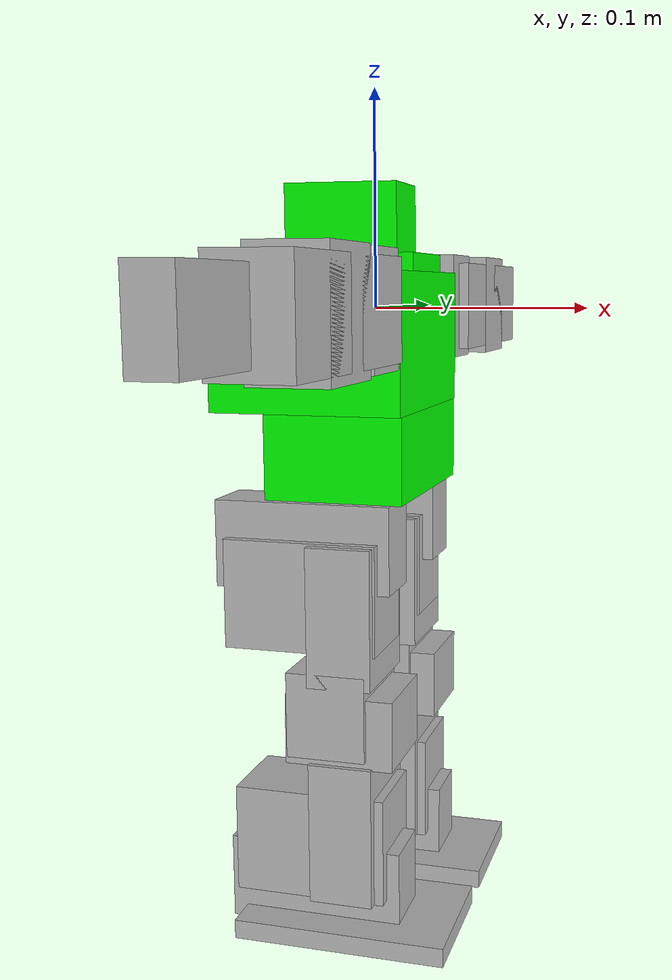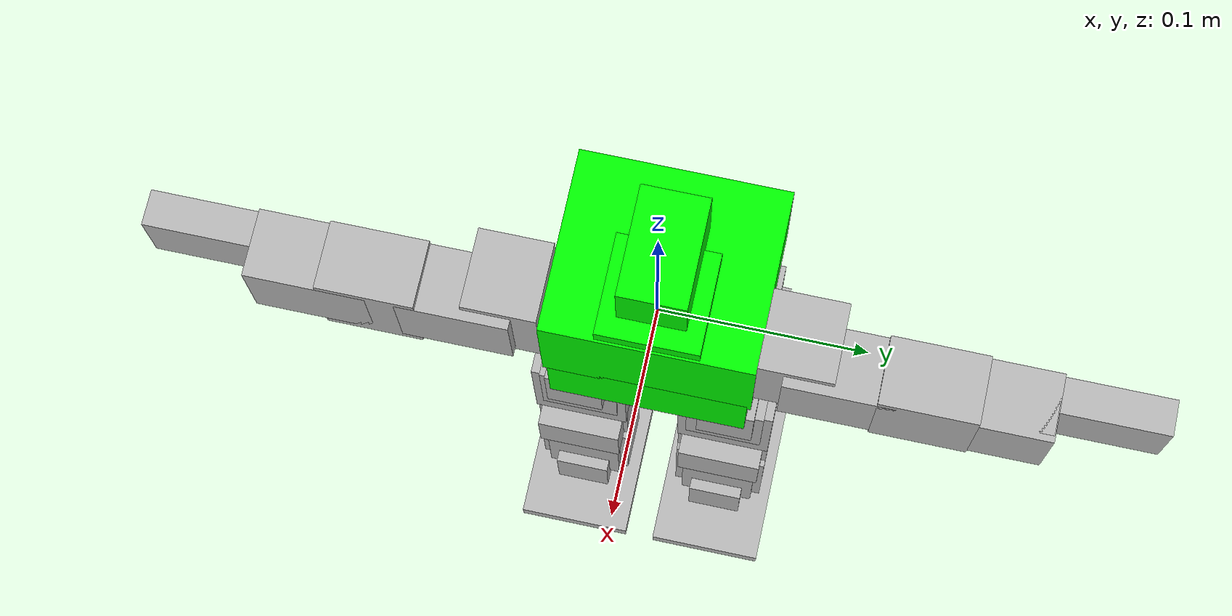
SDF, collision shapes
<sdf version='1.11'>
  <model name='typea'>
    <link name='base_link'>
      <inertial>
        <pose>0.015744558693093009 0.0048437788455023426 0.0037645630991576988 0 0 0</pose>
        <mass>3.5780266466000001</mass>
        <inertia>
          <ixx>0.97981139318655797</ixx>
          <ixy>0.054338535077770631</ixy>
          <ixz>-0.0262127050067513</ixz>
          <iyy>0.97412561794500041</iyy>
          <iyz>0.019865925320662881</iyz>
          <izz>0.93638558858963594</izz>
        </inertia>
      </inertial>
      <collision name='base_link_fixed_joint_lump__head_collision_collision'>
        <pose>-0.012200000000000001 0 0.035000000000000003 0 0 0</pose>
        <geometry>
          <box>
            <size>0.053999999999999999 0.033000000000000002 0.043999999999999997</size>
          </box>
        </geometry>
      </collision>
      <collision name='base_link_fixed_joint_lump__torso_collision_top_collision_1'>
        <pose>-0.019 0 -0.014999999999999999 0 0 0</pose>
        <geometry>
          <box>
            <size>0.090499999999999997 0.10299999999999999 0.063500000000000001</size>
          </box>
        </geometry>
      </collision>
      <collision name='base_link_fixed_joint_lump__torso_collision_bottom_collision_2'>
        <pose>-0.0062500000000000003 0 -0.064799999999999996 0 0 0</pose>
        <geometry>
          <box>
            <size>0.065000000000000002 0.099000000000000005 0.042999999999999997</size>
          </box>
        </geometry>
      </collision>
      <collision name='base_link_fixed_joint_lump__head_collision_collision_3'>
        <pose>0 0 0 0 0 0</pose>
        <geometry>
          <box>
            <size>0.050000000000000003 0.050000000000000003 0.050000000000000003</size>
          </box>
        </geometry>
      </collision>
      <collision name='base_link_fixed_joint_lump__imu_link_collision_4'>
        <pose>0 0 0.050000000000000003 0 0 0</pose>
        <geometry>
          <box>
            <size>0.01 0.01 0.01</size>
          </box>
        </geometry>
      </collision>
      <visual name='base_link_fixed_joint_lump__torso_link_visual'>
        <pose>0 0 0 1.5707963267948959 -5.5511151231257827e-17 1.5707963267948959</pose>
        <geometry>
          <mesh>
            <scale>0.001 0.001 0.001</scale>
            <uri>file:///home/robkwan/ros2_ws/src/bioloid_description/assets/cad/BPF-CHEST-F_FCD-Conv_BDR-Col.dae</uri>
          </mesh>
        </geometry>
      </visual>
      <visual name='base_link_fixed_joint_lump__torso_link_visual_1'>
        <pose>0 0 0 1.5707963267948959 -5.5511151231257827e-17 1.5707963267948959</pose>
        <geometry>
          <mesh>
            <scale>0.001 0.001 0.001</scale>
            <uri>file:///home/robkwan/ros2_ws/src/bioloid_description/assets/cad/BPF-CHEST-B_FCD-Conv_BDR-Col.dae</uri>
          </mesh>
        </geometry>
      </visual>
      <visual name='base_link_fixed_joint_lump__torso_link_visual_2'>
        <pose>-0.032000000000000001 0 -0.014999999999999999 -3.1415926535897931 1.2246467991473527e-16 -1.570796326794897</pose>
        <geometry>
          <mesh>
            <scale>0.001 0.001 0.001</scale>
            <uri>file:///home/robkwan/ros2_ws/src/bioloid_description/assets/cad/CM-5_FCD-Conv_BDR-Col.dae</uri>
          </mesh>
        </geometry>
      </visual>
      <visual name='base_link_fixed_joint_lump__torso_link_visual_3'>
        <pose>0 0 0.025000000000000001 -1.5707963267948959 -5.5511151231257827e-17 -1.5707963267948959</pose>
        <geometry>
          <mesh>
            <scale>0.001 0.001 0.001</scale>
            <uri>file:///home/robkwan/ros2_ws/src/bioloid_description/assets/cad/AX-S1_FCD-Conv_BDR-Col.dae</uri>
          </mesh>
        </geometry>
      </visual>
      <visual name='base_link_fixed_joint_lump__torso_link_visual_4'>
        <pose>0 -0.032000000000000001 0 1.5707963267948959 0 0</pose>
        <geometry>
          <mesh>
            <scale>0.001 0.001 0.001</scale>
            <uri>file:///home/robkwan/ros2_ws/src/bioloid_description/assets/cad/AX-12_FCD-Conv_BDR-Col.dae</uri>
          </mesh>
        </geometry>
      </visual>
      <visual name='base_link_fixed_joint_lump__torso_link_visual_5'>
        <pose>-0.019 -0.032000000000000001 -0.014500000000000001 -1.5707963267948968 -1.5707963118937354 0</pose>
        <geometry>
          <mesh>
            <scale>0.001 0.001 0.001</scale>
            <uri>file:///home/robkwan/ros2_ws/src/bioloid_description/assets/cad/FP04-F3_FCD-Conv_BDR-Col.dae</uri>
          </mesh>
        </geometry>
      </visual>
      <visual name='base_link_fixed_joint_lump__torso_link_visual_6'>
        <pose>0 0.032000000000000001 0 1.5707963267948959 3.7109275873535113e-33 3.1415926535897931</pose>
        <geometry>
          <mesh>
            <scale>0.001 0.001 0.001</scale>
            <uri>file:///home/robkwan/ros2_ws/src/bioloid_description/assets/cad/AX-12_FCD-Conv_BDR-Col.dae</uri>
          </mesh>
        </geometry>
      </visual>
      <visual name='base_link_fixed_joint_lump__torso_link_visual_7'>
        <pose>-0.019 0.032000000000000001 -0.014500000000000001 -1.5707963267948968 -1.5707963118937354 0</pose>
        <geometry>
          <mesh>
            <scale>0.001 0.001 0.001</scale>
            <uri>file:///home/robkwan/ros2_ws/src/bioloid_description/assets/cad/FP04-F3_FCD-Conv_BDR-Col.dae</uri>
          </mesh>
        </geometry>
      </visual>
      <visual name='base_link_fixed_joint_lump__torso_link_visual_8'>
        <pose>0.017500000000000002 0 -0.065500000000000003 0 0 1.5707963267948959</pose>
        <geometry>
          <mesh>
            <scale>0.001 0.001 0.001</scale>
            <uri>file:///home/robkwan/ros2_ws/src/bioloid_description/assets/cad/FP04-F3_FCD-Conv_BDR-Col.dae</uri>
          </mesh>
        </geometry>
      </visual>
      <visual name='base_link_fixed_joint_lump__torso_link_visual_9'>
        <pose>-0.017500000000000002 0 -0.065500000000000003 0 0 -1.5707963267948959</pose>
        <geometry>
          <mesh>
            <scale>0.001 0.001 0.001</scale>
            <uri>file:///home/robkwan/ros2_ws/src/bioloid_description/assets/cad/FP04-F3_FCD-Conv_BDR-Col.dae</uri>
          </mesh>
        </geometry>
      </visual>
      <visual name='base_link_fixed_joint_lump__torso_link_visual_10'>
        <pose>0 -0.0385 -0.065500000000000003 3.1415926535897931 1.224646799147353e-16 -1.224646799147353e-16</pose>
        <geometry>
          <mesh>
            <scale>0.001 0.001 0.001</scale>
            <uri>file:///home/robkwan/ros2_ws/src/bioloid_description/assets/cad/AX-12_FCD-Conv_BDR-Col.dae</uri>
          </mesh>
        </geometry>
      </visual>
      <visual name='base_link_fixed_joint_lump__torso_link_visual_11'>
        <pose>0 0.0385 -0.065500000000000003 3.1415926535897931 1.224646799147353e-16 3.1415926535897931</pose>
        <geometry>
          <mesh>
            <scale>0.001 0.001 0.001</scale>
            <uri>file:///home/robkwan/ros2_ws/src/bioloid_description/assets/cad/AX-12_FCD-Conv_BDR-Col.dae</uri>
          </mesh>
        </geometry>
      </visual>
      <visual name='base_link_fixed_joint_lump__head_link_visual_12'>
        <pose>0 0 0 0 0 0</pose>
        <geometry>
          <mesh>
            <scale>1 1 1</scale>
            <uri>file:///home/robkwan/ros2_ws/src/bioloid_description/assets/cad/Bioloid_CUERPO_vis_4.dae</uri>
          </mesh>
        </geometry>
      </visual>
      <visual name='base_link_fixed_joint_lump__imu_link_visual_13'>
        <pose>0 0 0.050000000000000003 0 0 0</pose>
        <geometry>
          <box>
            <size>0.040000000000000001 0.02 0.0050000000000000001</size>
          </box>
        </geometry>
        <material>
          <diffuse>0 1 0 1</diffuse>
          <ambient>0 1 0 1</ambient>
        </material>
      </visual>
      <self_collide>false</self_collide>
    </link>
    <joint name='head2_joint' type='revolute'>
      <pose relative_to='base_link'>0 0 0 0 0 0</pose>
      <parent>base_link</parent>
      <child>head2_link</child>
      <axis>
        <xyz>0 0 1</xyz>
        <limit>
          <lower>-1</lower>
          <upper>1</upper>
          <effort>1.5</effort>
          <velocity>1</velocity>
        </limit>
        <dynamics>
          <spring_reference>0</spring_reference>
          <spring_stiffness>0</spring_stiffness>
        </dynamics>
      </axis>
    </joint>
    <link name='head2_link'>
      <pose relative_to='head2_joint'>0 0 0 0 0 0</pose>
      <inertial>
        <pose>0 0 0 0 0 0</pose>
        <mass>0.10000000000000001</mass>
        <inertia>
          <ixx>0.001</ixx>
          <ixy>0</ixy>
          <ixz>0</ixz>
          <iyy>0.001</iyy>
          <iyz>0</iyz>
          <izz>0.001</izz>
        </inertia>
      </inertial>
      <collision name='head2_link_fixed_joint_lump__head2_collision_collision'>
        <pose>0 0 0 0 0 0</pose>
        <geometry>
          <box>
            <size>0.050000000000000003 0.050000000000000003 0.050000000000000003</size>
          </box>
        </geometry>
      </collision>
      <visual name='head2_link_visual'>
        <pose>0 0 0 0 0 0</pose>
        <geometry>
          <mesh>
            <scale>1 1 1</scale>
            <uri>file:///home/robkwan/ros2_ws/src/bioloid_description/assets/cad/Bioloid_CUERPO_vis_2.dae</uri>
          </mesh>
        </geometry>
      </visual>
    </link>
    <joint name='l_hip_twist_joint' type='revolute'>
      <pose relative_to='base_link'>0 0.0385 -0.065500000000000003 3.1415926535897931 1.2246467991473527e-16 1.570796326794897</pose>
      <parent>base_link</parent>
      <child>l_hip_twist_link</child>
      <axis>
        <xyz>0 0 1</xyz>
        <limit>
          <lower>-0.5</lower>
          <upper>0.5</upper>
          <effort>10</effort>
          <velocity>5.6548667999999997</velocity>
        </limit>
        <dynamics>
          <spring_reference>0</spring_reference>
          <spring_stiffness>0</spring_stiffness>
        </dynamics>
      </axis>
    </joint>
    <link name='l_hip_twist_link'>
      <pose relative_to='l_hip_twist_joint'>0 0 0 0 0 0</pose>
      <inertial>
        <pose>0.0005416307 -9.1999999999999998e-07 0.0190685105 0 0 0</pose>
        <mass>0.075519362300000004</mass>
        <inertia>
          <ixx>0.0082750315000000001</ixx>
          <ixy>-1.0509999999999999e-07</ixy>
          <ixz>0.00026811929999999998</ixz>
          <iyy>0.019481498399999998</iyy>
          <iyz>-5.5020000000000004e-07</iyz>
          <izz>0.0133677616</izz>
        </inertia>
      </inertial>
      <collision name='l_hip_twist_link_fixed_joint_lump__r_hip_twist_collision_collision'>
        <pose>0.00080000000000000004 -0.02 0.041000000000000002 0 0 0</pose>
        <geometry>
          <box>
            <size>0.029000000000000001 0.083000000000000004 0.040500000000000001</size>
          </box>
        </geometry>
      </collision>
      <visual name='l_hip_twist_link_visual'>
        <pose>0 -0.02 0.050000000000000003 3.1415926535897931 0 0</pose>
        <geometry>
          <mesh>
            <scale>0.001 0.001 0.001</scale>
            <uri>file:///home/robkwan/ros2_ws/src/bioloid_description/assets/cad/FP04-F5_FCD-Conv_BDR-Col.dae</uri>
          </mesh>
        </geometry>
      </visual>
    </link>
    <joint name='l_hip_lateral_joint' type='revolute'>
      <pose relative_to='l_hip_twist_link'>0 0 0.050000000000000003 1.5707963267948959 0 0</pose>
      <parent>l_hip_twist_link</parent>
      <child>l_hip_lateral_link</child>
      <axis>
        <xyz>0 0 1</xyz>
        <limit>
          <lower>-0.80000000000000004</lower>
          <upper>0.80000000000000004</upper>
          <effort>10</effort>
          <velocity>5.6548667999999997</velocity>
        </limit>
        <dynamics>
          <spring_reference>0</spring_reference>
          <spring_stiffness>0</spring_stiffness>
        </dynamics>
      </axis>
    </joint>
    <link name='l_hip_lateral_link'>
      <pose relative_to='l_hip_lateral_joint'>0 0 0 0 0 0</pose>
      <inertial>
        <pose>0.018349903899999999 0.0023512250000000002 0.0035241953 0 0 0</pose>
        <mass>0.68524293629999999</mass>
        <inertia>
          <ixx>0.015290407799999999</ixx>
          <ixy>0.012548178300000001</ixy>
          <ixz>0.015637424800000001</ixz>
          <iyy>0.10502674989999999</iyy>
          <iyz>0.0020800084000000001</iyz>
          <izz>0.1059474294</izz>
        </inertia>
      </inertial>
      <collision name='l_hip_lateral_link_fixed_joint_lump__r_hip_lateral_collision_collision'>
        <pose>0 0.0135 0.02 0 0 0</pose>
        <geometry>
          <box>
            <size>0.040000000000000001 0.050999999999999997 0.072099999999999997</size>
          </box>
        </geometry>
      </collision>
      <visual name='l_hip_lateral_link_visual'>
        <pose>0 0 0.035299999999999998 0 0 3.1415926535897931</pose>
        <geometry>
          <mesh>
            <scale>0.001 0.001 0.001</scale>
            <uri>file:///home/robkwan/ros2_ws/src/bioloid_description/assets/cad/AX-12_FCD-Conv_BDR-Col.dae</uri>
          </mesh>
        </geometry>
      </visual>
      <visual name='l_hip_lateral_link_visual_1'>
        <pose>0.019 0.014500000000000001 0.051299999999999998 1.5707963267948957 -1.5707963267948966 0</pose>
        <geometry>
          <mesh>
            <scale>0.001 0.001 0.001</scale>
            <uri>file:///home/robkwan/ros2_ws/src/bioloid_description/assets/cad/FP04-F6_FCD-Conv_BDR-Col.dae</uri>
          </mesh>
        </geometry>
      </visual>
      <visual name='l_hip_lateral_link_visual_2'>
        <pose>-0.019 0.014500000000000001 0.051299999999999998 -1.5707963267948957 -1.5707963267948966 0</pose>
        <geometry>
          <mesh>
            <scale>0.001 0.001 0.001</scale>
            <uri>file:///home/robkwan/ros2_ws/src/bioloid_description/assets/cad/FP04-F6_FCD-Conv_BDR-Col.dae</uri>
          </mesh>
        </geometry>
      </visual>
      <visual name='l_hip_lateral_link_visual_3'>
        <pose>0 0 0.0032999999999999969 3.1415926535897931 1.5707963267948966 0</pose>
        <geometry>
          <mesh>
            <scale>0.001 0.001 0.001</scale>
            <uri>file:///home/robkwan/ros2_ws/src/bioloid_description/assets/cad/AX-12_FCD-Conv_BDR-Col.dae</uri>
          </mesh>
        </geometry>
      </visual>
      <visual name='l_hip_lateral_link_visual_4'>
        <pose>0 0 -0.0147 -1.570796326794897 1.2246467991473527e-16 -3.1415926535897931</pose>
        <geometry>
          <mesh>
            <scale>0.001 0.001 0.001</scale>
            <uri>file:///home/robkwan/ros2_ws/src/bioloid_description/assets/cad/BPF-BU_FCD-Conv_BDR-Col.dae</uri>
          </mesh>
        </geometry>
      </visual>
      <visual name='l_hip_lateral_link_visual_5'>
        <pose>0 0.014500000000000001 -0.015699999999999999 1.5707963267948972 5.5511151231257827e-17 -1.5707963267948972</pose>
        <geometry>
          <mesh>
            <scale>0.001 0.001 0.001</scale>
            <uri>file:///home/robkwan/ros2_ws/src/bioloid_description/assets/cad/FP04-F7_FCD-Conv_BDR-Col.dae</uri>
          </mesh>
        </geometry>
      </visual>
    </link>
    <joint name='l_hip_swing_joint' type='revolute'>
      <pose relative_to='l_hip_lateral_link'>0 0 0 1.5707963267948959 5.5511151231257827e-17 -1.5707963267948959</pose>
      <parent>l_hip_lateral_link</parent>
      <child>l_upper_leg_link</child>
      <axis>
        <xyz>0 0 1</xyz>
        <limit>
          <lower>-0.39999999999999991</lower>
          <upper>2</upper>
          <effort>10</effort>
          <velocity>5.6548667999999997</velocity>
        </limit>
        <dynamics>
          <spring_reference>0</spring_reference>
          <spring_stiffness>0</spring_stiffness>
        </dynamics>
      </axis>
    </joint>
    <link name='l_upper_leg_link'>
      <pose relative_to='l_hip_swing_joint'>0 0 0 0 0 0</pose>
      <inertial>
        <pose>-0.0012110096000000001 5.6799999999999999e-08 -0.044407489500000001 0 0 0</pose>
        <mass>0.1557654222</mass>
        <inertia>
          <ixx>0.086797553799999996</ixx>
          <ixy>-2.55e-08</ixy>
          <ixz>0.0030686266999999999</ixz>
          <iyy>0.078400559600000003</iyy>
          <iyz>-8.7499999999999996e-08</iyz>
          <izz>0.013867953299999999</izz>
        </inertia>
      </inertial>
      <collision name='l_upper_leg_link_fixed_joint_lump__r_upper_leg_proximal_collision_collision'>
        <pose>-0.021399999999999999 0 0 0 0 0</pose>
        <geometry>
          <box>
            <size>0.065000000000000002 0.029999999999999999 0.049000000000000002</size>
          </box>
        </geometry>
      </collision>
      <collision name='l_upper_leg_link_fixed_joint_lump__r_upper_leg_distal_collision_collision_1'>
        <pose>-0.067500000000000004 0.0064999999999999997 0 0 0 0</pose>
        <geometry>
          <box>
            <size>0.040000000000000001 0.037100000000000001 0.049000000000000002</size>
          </box>
        </geometry>
      </collision>
      <visual name='l_upper_leg_link_visual'>
        <pose>0 0 0 3.1415926535897931 1.5707963267948966 0</pose>
        <geometry>
          <mesh>
            <scale>0.001 0.001 0.001</scale>
            <uri>file:///home/robkwan/ros2_ws/src/bioloid_description/assets/cad/FP04-F4_FCD-Conv_BDR-Col.dae</uri>
          </mesh>
        </geometry>
      </visual>
      <visual name='l_upper_leg_link_visual_1'>
        <pose>-0.074999999999999997 0.014500000000000001 0 3.1415926535897931 -1.5707963267948966 0</pose>
        <geometry>
          <mesh>
            <scale>0.001 0.001 0.001</scale>
            <uri>file:///home/robkwan/ros2_ws/src/bioloid_description/assets/cad/FP04-F1_FCD-Conv_BDR-Col.dae</uri>
          </mesh>
        </geometry>
      </visual>
    </link>
    <joint name='l_knee_joint' type='revolute'>
      <pose relative_to='l_upper_leg_link'>-0.074999999999999997 0.014500000000000001 0 0 0 0</pose>
      <parent>l_upper_leg_link</parent>
      <child>l_lower_leg_link</child>
      <axis>
        <xyz>0 0 1</xyz>
        <limit>
          <lower>-2</lower>
          <upper>0</upper>
          <effort>10</effort>
          <velocity>5.6548667999999997</velocity>
        </limit>
        <dynamics>
          <spring_reference>0</spring_reference>
          <spring_stiffness>0</spring_stiffness>
        </dynamics>
      </axis>
    </joint>
    <link name='l_lower_leg_link'>
      <pose relative_to='l_knee_joint'>0 0 0 0 0 0</pose>
      <inertial>
        <pose>-0.0010052500000000001 0.00026745909999999998 -0.0110862203 0 0 0</pose>
        <mass>0.43260893350000001</mass>
        <inertia>
          <ixx>0.054159649999999997</ixx>
          <ixy>-0.000124568</ixy>
          <ixz>0.0010887872</ixz>
          <iyy>0.0479327482</iyy>
          <iyz>-0.00095904110000000003</iyz>
          <izz>0.013609731999999999</izz>
        </inertia>
      </inertial>
      <collision name='l_lower_leg_link_fixed_joint_lump__r_lower_leg_proximal_collision_collision'>
        <pose>0 -0.0135 0 0 0 0</pose>
        <geometry>
          <box>
            <size>0.033000000000000002 0.050999999999999997 0.043999999999999997</size>
          </box>
        </geometry>
      </collision>
      <collision name='l_lower_leg_link_fixed_joint_lump__r_lower_leg_distal_collision_collision_1'>
        <pose>-0.049200000000000001 -0.014500000000000001 0 0 0 0</pose>
        <geometry>
          <box>
            <size>0.067000000000000004 0.029999999999999999 0.049000000000000002</size>
          </box>
        </geometry>
      </collision>
      <visual name='l_lower_leg_link_visual'>
        <pose>0 0 0 0 0 0</pose>
        <geometry>
          <mesh>
            <scale>0.001 0.001 0.001</scale>
            <uri>file:///home/robkwan/ros2_ws/src/bioloid_description/assets/cad/AX-12_FCD-Conv_BDR-Col.dae</uri>
          </mesh>
        </geometry>
      </visual>
      <visual name='l_lower_leg_link_visual_1'>
        <pose>-0.019 -0.014500000000000001 0 0 0 -1.5707963267948959</pose>
        <geometry>
          <mesh>
            <scale>0.001 0.001 0.001</scale>
            <uri>file:///home/robkwan/ros2_ws/src/bioloid_description/assets/cad/FP04-F3_FCD-Conv_BDR-Col.dae</uri>
          </mesh>
        </geometry>
      </visual>
      <visual name='l_lower_leg_link_visual_2'>
        <pose>-0.070999999999999994 -0.014500000000000001 0 -3.1415926535897931 -1.5707963267948966 0</pose>
        <geometry>
          <mesh>
            <scale>0.001 0.001 0.001</scale>
            <uri>file:///home/robkwan/ros2_ws/src/bioloid_description/assets/cad/FP04-F4_FCD-Conv_BDR-Col.dae</uri>
          </mesh>
        </geometry>
      </visual>
    </link>
    <joint name='l_ankle_swing_joint' type='revolute'>
      <pose relative_to='l_lower_leg_link'>-0.070999999999999994 -0.014500000000000001 0 3.1415926535897931 0 0</pose>
      <parent>l_lower_leg_link</parent>
      <child>l_ankle_swing_link</child>
      <axis>
        <xyz>0 0 1</xyz>
        <limit>
          <lower>-2</lower>
          <upper>0.39999999999999991</upper>
          <effort>10</effort>
          <velocity>5.6548667999999997</velocity>
        </limit>
        <dynamics>
          <spring_reference>0</spring_reference>
          <spring_stiffness>0</spring_stiffness>
        </dynamics>
      </axis>
    </joint>
    <link name='l_ankle_swing_link'>
      <pose relative_to='l_ankle_swing_joint'>0 0 0 0 0 0</pose>
      <inertial>
        <pose>0.016750927799999999 0.0033519499999999998 -0.0035241956000000001 0 0 0</pose>
        <mass>0.68524293629999999</mass>
        <inertia>
          <ixx>0.016068747500000001</ixx>
          <ixy>0.013526458599999999</ixy>
          <ixz>-0.014299952100000001</ixz>
          <iyy>0.090344558599999999</iyy>
          <iyz>-0.0025649497000000002</iyz>
          <izz>0.092043507999999996</izz>
        </inertia>
      </inertial>
      <collision name='l_ankle_swing_link_fixed_joint_lump__r_ankle_swing_collision_collision'>
        <pose>0.0135 -0.0167 0 0 0 0</pose>
        <geometry>
          <box>
            <size>0.050999999999999997 0.072099999999999997 0.040000000000000001</size>
          </box>
        </geometry>
      </collision>
      <visual name='l_ankle_swing_link_visual'>
        <pose>0 0 0 3.1415926535897931 -1.0033023363942468e-32 -1.5707963267948959</pose>
        <geometry>
          <mesh>
            <scale>0.001 0.001 0.001</scale>
            <uri>file:///home/robkwan/ros2_ws/src/bioloid_description/assets/cad/AX-12_FCD-Conv_BDR-Col.dae</uri>
          </mesh>
        </geometry>
      </visual>
      <visual name='l_ankle_swing_link_visual_1'>
        <pose>0.014500000000000001 0.019 0 -1.224646799147353e-16 1.224646799147353e-16 3.1415926535897931</pose>
        <geometry>
          <mesh>
            <scale>0.001 0.001 0.001</scale>
            <uri>file:///home/robkwan/ros2_ws/src/bioloid_description/assets/cad/FP04-F7_FCD-Conv_BDR-Col.dae</uri>
          </mesh>
        </geometry>
      </visual>
      <visual name='l_ankle_swing_link_visual_2'>
        <pose>0 -0.032000000000000001 0 1.5707963267948957 -1.5707963267948966 0</pose>
        <geometry>
          <mesh>
            <scale>0.001 0.001 0.001</scale>
            <uri>file:///home/robkwan/ros2_ws/src/bioloid_description/assets/cad/AX-12_FCD-Conv_BDR-Col.dae</uri>
          </mesh>
        </geometry>
      </visual>
      <visual name='l_ankle_swing_link_visual_3'>
        <pose>0.014500000000000001 -0.048000000000000001 -0.019 1.5707963267948959 5.5511151231257827e-17 -1.5707963267948959</pose>
        <geometry>
          <mesh>
            <scale>0.001 0.001 0.001</scale>
            <uri>file:///home/robkwan/ros2_ws/src/bioloid_description/assets/cad/FP04-F6_FCD-Conv_BDR-Col.dae</uri>
          </mesh>
        </geometry>
      </visual>
      <visual name='l_ankle_swing_link_visual_4'>
        <pose>0.014500000000000001 -0.048000000000000001 0.019 -1.5707963267948959 -5.5511151231257827e-17 -1.5707963267948959</pose>
        <geometry>
          <mesh>
            <scale>0.001 0.001 0.001</scale>
            <uri>file:///home/robkwan/ros2_ws/src/bioloid_description/assets/cad/FP04-F6_FCD-Conv_BDR-Col.dae</uri>
          </mesh>
        </geometry>
      </visual>
    </link>
    <joint name='l_ankle_lateral_joint' type='revolute'>
      <pose relative_to='l_ankle_swing_link'>0 0 0 -1.5707963267948959 0 0</pose>
      <parent>l_ankle_swing_link</parent>
      <child>l_ankle_lateral_link</child>
      <axis>
        <xyz>0 0 1</xyz>
        <limit>
          <lower>-0.80000000000000004</lower>
          <upper>0.80000000000000004</upper>
          <effort>10</effort>
          <velocity>5.6548667999999997</velocity>
        </limit>
        <dynamics>
          <spring_reference>0</spring_reference>
          <spring_stiffness>0</spring_stiffness>
        </dynamics>
      </axis>
    </joint>
    <link name='l_ankle_lateral_link'>
      <pose relative_to='l_ankle_lateral_joint'>0 0 0 0 0 0</pose>
      <inertial>
        <pose>-0.0055676472000000003 -0.0035014439999999998 0.0028465215 0 0 0</pose>
        <mass>0.37356021979999998</mass>
        <inertia>
          <ixx>0.0246875794</ixx>
          <ixy>0.00266584</ixy>
          <ixz>-0.0028084080000000001</ixz>
          <iyy>0.070321858400000006</iyy>
          <iyz>-0.0022985321999999999</iyz>
          <izz>0.082201725599999997</izz>
        </inertia>
      </inertial>
      <collision name='l_ankle_lateral_link_fixed_joint_lump__r_ankle_lateral_collision_collision'>
        <pose>-0.0089999999999999993 0 -0.016 0 0 0</pose>
        <geometry>
          <box>
            <size>0.040500000000000001 0.029000000000000001 0.083000000000000004</size>
          </box>
        </geometry>
      </collision>
      <collision name='l_ankle_lateral_link_fixed_joint_lump__l_foot_collision_collision_1'>
        <pose>-0.027699999999999999 0 0 0 0 0</pose>
        <geometry>
          <box>
            <size>0.0089999999999999993 0.060999999999999999 0.10100000000000001</size>
          </box>
        </geometry>
      </collision>
      <visual name='l_ankle_lateral_link_visual'>
        <pose>0 0 0.014999999999999999 1.5707963267948959 0 0</pose>
        <geometry>
          <mesh>
            <scale>0.001 0.001 0.001</scale>
            <uri>file:///home/robkwan/ros2_ws/src/bioloid_description/assets/cad/BPF-BU_FCD-Conv_BDR-Col.dae</uri>
          </mesh>
        </geometry>
      </visual>
      <visual name='l_ankle_lateral_link_visual_1'>
        <pose>0 0 -0.0155 -1.5707963267948972 5.5511151231257827e-17 1.5707963267948972</pose>
        <geometry>
          <mesh>
            <scale>0.001 0.001 0.001</scale>
            <uri>file:///home/robkwan/ros2_ws/src/bioloid_description/assets/cad/FP04-F5_FCD-Conv_BDR-Col.dae</uri>
          </mesh>
        </geometry>
      </visual>
      <visual name='l_ankle_lateral_link_fixed_joint_lump__l_foot_link_visual_2'>
        <pose>-0.0235 0 0 -1.5707963267948968 1.5707963118937354 0</pose>
        <geometry>
          <mesh>
            <scale>0.001 0.001 0.001</scale>
            <uri>file:///home/robkwan/ros2_ws/src/bioloid_description/assets/cad/FP04-F12_FCD-Conv_BDR-Col.dae</uri>
          </mesh>
        </geometry>
      </visual>
    </link>
    <joint name='l_shoulder_swing_joint' type='revolute'>
      <pose relative_to='base_link'>0 0.032000000000000001 0 -1.5707963267948957 -1.5707963267948966 0</pose>
      <parent>base_link</parent>
      <child>l_shoulder_swing_link</child>
      <axis>
        <xyz>0 0 1</xyz>
        <limit>
          <lower>-1</lower>
          <upper>1.570796326794897</upper>
          <effort>2.7999999999999998</effort>
          <velocity>1</velocity>
        </limit>
        <dynamics>
          <spring_reference>0</spring_reference>
          <spring_stiffness>0</spring_stiffness>
        </dynamics>
      </axis>
    </joint>
    <link name='l_shoulder_swing_link'>
      <pose relative_to='l_shoulder_swing_joint'>0 0 0 0 0 0</pose>
      <inertial>
        <pose>-0.0109359544 -0.0123630374 6.9999999999999996e-10 0 0 0</pose>
        <mass>0.059594581600000002</mass>
        <inertia>
          <ixx>0.0069903407000000001</ixx>
          <ixy>0.0020812370000000001</ixy>
          <ixz>-1e-10</ixz>
          <iyy>0.0067210938999999999</iyy>
          <iyz>-2.0000000000000001e-10</iyz>
          <izz>0.0054521982999999998</izz>
        </inertia>
      </inertial>
      <collision name='l_shoulder_swing_link_fixed_joint_lump__l_shoulder_collision_collision'>
        <pose>0 0.0060000000000000001 0.037499999999999999 0 0 0</pose>
        <geometry>
          <box>
            <size>0.051999999999999998 0.039 0.035999999999999997</size>
          </box>
        </geometry>
      </collision>
      <visual name='l_shoulder_swing_link_visual'>
        <pose>0 0.014 0.043999999999999997 3.1415926535897931 1.224646799147353e-16 -1.224646799147353e-16</pose>
        <geometry>
          <mesh>
            <scale>0.001 0.001 0.001</scale>
            <uri>file:///home/robkwan/ros2_ws/src/bioloid_description/assets/cad/FP04-F1_FCD-Conv_BDR-Col.dae</uri>
          </mesh>
        </geometry>
      </visual>
    </link>
    <joint name='l_shoulder_lateral_joint' type='revolute'>
      <pose relative_to='l_shoulder_swing_link'>0 0.014 0.043999999999999997 0 -1.5707963267948966 0</pose>
      <parent>l_shoulder_swing_link</parent>
      <child>l_upper_arm_link</child>
      <axis>
        <xyz>0 0 1</xyz>
        <limit>
          <lower>-1.5</lower>
          <upper>1.5</upper>
          <effort>2.7999999999999998</effort>
          <velocity>1</velocity>
        </limit>
        <dynamics>
          <spring_reference>0</spring_reference>
          <spring_stiffness>0</spring_stiffness>
        </dynamics>
      </axis>
    </joint>
    <link name='l_upper_arm_link'>
      <pose relative_to='l_shoulder_lateral_joint'>0 0 0 0 0 0</pose>
      <inertial>
        <pose>2.0319999999999999e-07 0.0068291604000000001 -0.00067105520000000001 0 0 0</pose>
        <mass>0.38228707340000001</mass>
        <inertia>
          <ixx>0.027469089200000001</ixx>
          <ixy>4.066e-07</ixy>
          <ixz>8.5899999999999995e-08</ixz>
          <iyy>0.0077817002</iyy>
          <iyz>-0.00071390120000000004</iyz>
          <izz>0.022603475899999999</izz>
        </inertia>
      </inertial>
      <collision name='l_upper_arm_link_fixed_joint_lump__l_upper arm_collision_proximal_collision'>
        <pose>0.014800000000000001 0 0 0 0 0</pose>
        <geometry>
          <box>
            <size>0.053999999999999999 0.033000000000000002 0.043999999999999997</size>
          </box>
        </geometry>
      </collision>
      <collision name='l_upper_arm_link_fixed_joint_lump__l_upper arm_collision_distal_collision_1'>
        <pose>0.055500000000000001 0 0 0 0 0</pose>
        <geometry>
          <box>
            <size>0.047 0.033000000000000002 0.051999999999999998</size>
          </box>
        </geometry>
      </collision>
      <visual name='l_upper_arm_link_visual'>
        <pose>0 0 0 3.1415926535897931 -1.0033023363942468e-32 -1.5707963267948959</pose>
        <geometry>
          <mesh>
            <scale>0.001 0.001 0.001</scale>
            <uri>file:///home/robkwan/ros2_ws/src/bioloid_description/assets/cad/AX-12_FCD-Conv_BDR-Col.dae</uri>
          </mesh>
        </geometry>
      </visual>
      <visual name='l_upper_arm_link_visual_1'>
        <pose>0 0 0.018499999999999999 1.5707963267948959 -5.5511151231257827e-17 1.5707963267948959</pose>
        <geometry>
          <mesh>
            <scale>0.001 0.001 0.001</scale>
            <uri>file:///home/robkwan/ros2_ws/src/bioloid_description/assets/cad/BPF-BU_FCD-Conv_BDR-Col.dae</uri>
          </mesh>
        </geometry>
      </visual>
      <visual name='l_upper_arm_link_visual_2'>
        <pose>0 0 0.019 1.5707963267948959 -5.5511151231257827e-17 1.5707963267948959</pose>
        <geometry>
          <mesh>
            <scale>0.001 0.001 0.001</scale>
            <uri>file:///home/robkwan/ros2_ws/src/bioloid_description/assets/cad/BPF-WA_FCD-Conv_BDR-Col.dae</uri>
          </mesh>
        </geometry>
      </visual>
      <visual name='l_upper_arm_link_visual_3'>
        <pose>0.041500000000000002 0 0 3.1415926535897931 -1.0033023363942468e-32 -1.5707963267948959</pose>
        <geometry>
          <mesh>
            <scale>0.001 0.001 0.001</scale>
            <uri>file:///home/robkwan/ros2_ws/src/bioloid_description/assets/cad/FP04-F3_FCD-Conv_BDR-Col.dae</uri>
          </mesh>
        </geometry>
      </visual>
      <visual name='l_upper_arm_link_visual_4'>
        <pose>0.067500000000000004 0 0 3.1415926535897931 1.5707963267948966 0</pose>
        <geometry>
          <mesh>
            <scale>0.001 0.001 0.001</scale>
            <uri>file:///home/robkwan/ros2_ws/src/bioloid_description/assets/cad/FP04-F2_FCD-Conv_BDR-Col.dae</uri>
          </mesh>
        </geometry>
      </visual>
    </link>
    <joint name='l_elbow_joint' type='revolute'>
      <pose relative_to='l_upper_arm_link'>0.067500000000000004 0 0 0 0 0</pose>
      <parent>l_upper_arm_link</parent>
      <child>l_lower_arm_link</child>
      <axis>
        <xyz>0 0 1</xyz>
        <limit>
          <lower>-1.77</lower>
          <upper>1.77</upper>
          <effort>2.7999999999999998</effort>
          <velocity>1</velocity>
        </limit>
        <dynamics>
          <spring_reference>0</spring_reference>
          <spring_stiffness>0</spring_stiffness>
        </dynamics>
      </axis>
    </joint>
    <link name='l_lower_arm_link'>
      <pose relative_to='l_elbow_joint'>0 0 0 0 0 0</pose>
      <inertial>
        <pose>-0.0005169352887581457 0.0079239450148689758 -0.00062177237368155763 0 0 0</pose>
        <mass>0.41258738969999997</mass>
        <inertia>
          <ixx>0.03292015515428607</ixx>
          <ixy>-0.0011233154062685979</ixy>
          <ixz>2.168663770537634e-07</ixz>
          <iyy>0.0091052028484069208</iyy>
          <iyz>-0.00071418455534468276</iyz>
          <izz>0.027986806816723522</izz>
        </inertia>
      </inertial>
      <collision name='l_lower_arm_link_fixed_joint_lump__l_lower_arm_collision_collision'>
        <pose>0.017000000000000001 0 0 0 0 0</pose>
        <geometry>
          <box>
            <size>0.058000000000000003 0.033000000000000002 0.043999999999999997</size>
          </box>
        </geometry>
      </collision>
      <collision name='l_lower_arm_link_fixed_joint_lump__l_palm_collision_collision_1'>
        <pose>0.039 0 0 0 0 0</pose>
        <geometry>
          <box>
            <size>0.013100000000000001 0.026499999999999999 0.043999999999999997</size>
          </box>
        </geometry>
      </collision>
      <collision name='l_lower_arm_link_fixed_joint_lump__l_fingers_collision_collision_2'>
        <pose>0.070099999999999996 -0.0077000000000000002 0 0 0 0</pose>
        <geometry>
          <box>
            <size>0.057500000000000002 0.017500000000000002 0.035000000000000003</size>
          </box>
        </geometry>
      </collision>
      <visual name='l_lower_arm_link_visual'>
        <pose>0 0 0 3.1415926535897931 -1.0033023363942468e-32 -1.5707963267948959</pose>
        <geometry>
          <mesh>
            <scale>0.001 0.001 0.001</scale>
            <uri>file:///home/robkwan/ros2_ws/src/bioloid_description/assets/cad/AX-12_FCD-Conv_BDR-Col.dae</uri>
          </mesh>
        </geometry>
      </visual>
      <visual name='l_lower_arm_link_visual_1'>
        <pose>0 0 0.018499999999999999 1.5707963267948959 -5.5511151231257827e-17 1.5707963267948959</pose>
        <geometry>
          <mesh>
            <scale>0.001 0.001 0.001</scale>
            <uri>file:///home/robkwan/ros2_ws/src/bioloid_description/assets/cad/BPF-BU_FCD-Conv_BDR-Col.dae</uri>
          </mesh>
        </geometry>
      </visual>
      <visual name='l_lower_arm_link_visual_2'>
        <pose>0 0 0.019 1.5707963267948959 -5.5511151231257827e-17 1.5707963267948959</pose>
        <geometry>
          <mesh>
            <scale>0.001 0.001 0.001</scale>
            <uri>file:///home/robkwan/ros2_ws/src/bioloid_description/assets/cad/BPF-WA_FCD-Conv_BDR-Col.dae</uri>
          </mesh>
        </geometry>
      </visual>
      <visual name='l_lower_arm_link_visual_3'>
        <pose>0.041500000000000002 0 0 3.1415926535897931 -1.0033023363942468e-32 -1.5707963267948959</pose>
        <geometry>
          <mesh>
            <scale>0.001 0.001 0.001</scale>
            <uri>file:///home/robkwan/ros2_ws/src/bioloid_description/assets/cad/FP04-F3_FCD-Conv_BDR-Col.dae</uri>
          </mesh>
        </geometry>
      </visual>
      <visual name='l_lower_arm_link_fixed_joint_lump__l_hand_link_visual_4'>
        <pose>0.041500000000000002 0 0 3.1415926535897931 -1.5707963267948966 0</pose>
        <geometry>
          <mesh>
            <scale>0.001 0.001 0.001</scale>
            <uri>file:///home/robkwan/ros2_ws/src/bioloid_description/assets/cad/FP04-F11_FCD-Conv_BDR-Col.dae</uri>
          </mesh>
        </geometry>
      </visual>
    </link>
    <joint name='r_hip_twist_joint' type='revolute'>
      <pose relative_to='base_link'>0 -0.0385 -0.065500000000000003 -3.1415926535897931 1.2246467991473527e-16 -1.570796326794897</pose>
      <parent>base_link</parent>
      <child>r_hip_twist_link</child>
      <axis>
        <xyz>0 0 1</xyz>
        <limit>
          <lower>-0.5</lower>
          <upper>0.5</upper>
          <effort>10</effort>
          <velocity>5.6548667999999997</velocity>
        </limit>
        <dynamics>
          <spring_reference>0</spring_reference>
          <spring_stiffness>0</spring_stiffness>
        </dynamics>
      </axis>
    </joint>
    <link name='r_hip_twist_link'>
      <pose relative_to='r_hip_twist_joint'>0 0 0 0 0 0</pose>
      <inertial>
        <pose>0.0005416307 -9.1999999999999998e-07 0.0190685105 0 0 0</pose>
        <mass>0.075519362300000004</mass>
        <inertia>
          <ixx>0.0082750315000000001</ixx>
          <ixy>-1.0509999999999999e-07</ixy>
          <ixz>0.00026811929999999998</ixz>
          <iyy>0.019481498399999998</iyy>
          <iyz>-5.5020000000000004e-07</iyz>
          <izz>0.0133677616</izz>
        </inertia>
      </inertial>
      <collision name='r_hip_twist_link_fixed_joint_lump__r_hip_twist_collision_collision'>
        <pose>0.00080000000000000004 0.02 0.041000000000000002 0 0 0</pose>
        <geometry>
          <box>
            <size>0.029000000000000001 0.083000000000000004 0.040500000000000001</size>
          </box>
        </geometry>
      </collision>
      <visual name='r_hip_twist_link_visual'>
        <pose>0 0.02 0.050000000000000003 3.1415926535897931 -3.0080778888518096e-49 3.1415926535897931</pose>
        <geometry>
          <mesh>
            <scale>0.001 0.001 0.001</scale>
            <uri>file:///home/robkwan/ros2_ws/src/bioloid_description/assets/cad/FP04-F5_FCD-Conv_BDR-Col.dae</uri>
          </mesh>
        </geometry>
      </visual>
    </link>
    <joint name='r_hip_lateral_joint' type='revolute'>
      <pose relative_to='r_hip_twist_link'>0 0 0.050000000000000003 -1.5707963267948959 0 0</pose>
      <parent>r_hip_twist_link</parent>
      <child>r_hip_lateral_link</child>
      <axis>
        <xyz>0 0 1</xyz>
        <limit>
          <lower>-0.80000000000000004</lower>
          <upper>0.80000000000000004</upper>
          <effort>10</effort>
          <velocity>5.6548667999999997</velocity>
        </limit>
        <dynamics>
          <spring_reference>0</spring_reference>
          <spring_stiffness>0</spring_stiffness>
        </dynamics>
      </axis>
    </joint>
    <link name='r_hip_lateral_link'>
      <pose relative_to='r_hip_lateral_joint'>0 0 0 0 0 0</pose>
      <inertial>
        <pose>0.016750927799999999 -0.0033519499999999998 0.0035241956000000001 0 0 0</pose>
        <mass>0.68524293629999999</mass>
        <inertia>
          <ixx>0.016068747500000001</ixx>
          <ixy>-0.013526458599999999</ixy>
          <ixz>0.014299952100000001</ixz>
          <iyy>0.090344558599999999</iyy>
          <iyz>-0.0025649497000000002</iyz>
          <izz>0.092043507999999996</izz>
        </inertia>
      </inertial>
      <collision name='r_hip_lateral_link_fixed_joint_lump__r_hip_lateral_collision_collision'>
        <pose>0 -0.0135 0.02 0 0 0</pose>
        <geometry>
          <box>
            <size>0.040000000000000001 0.050999999999999997 0.072099999999999997</size>
          </box>
        </geometry>
      </collision>
      <visual name='r_hip_lateral_link_visual'>
        <pose>0 0 0.035299999999999998 0 0 0</pose>
        <geometry>
          <mesh>
            <scale>0.001 0.001 0.001</scale>
            <uri>file:///home/robkwan/ros2_ws/src/bioloid_description/assets/cad/AX-12_FCD-Conv_BDR-Col.dae</uri>
          </mesh>
        </geometry>
      </visual>
      <visual name='r_hip_lateral_link_visual_1'>
        <pose>-0.019 -0.014500000000000001 0.051299999999999998 -1.5707963267948957 -1.5707963267948966 0</pose>
        <geometry>
          <mesh>
            <scale>0.001 0.001 0.001</scale>
            <uri>file:///home/robkwan/ros2_ws/src/bioloid_description/assets/cad/FP04-F6_FCD-Conv_BDR-Col.dae</uri>
          </mesh>
        </geometry>
      </visual>
      <visual name='r_hip_lateral_link_visual_2'>
        <pose>0.019 -0.014500000000000001 0.051299999999999998 1.5707963267948957 -1.5707963267948966 0</pose>
        <geometry>
          <mesh>
            <scale>0.001 0.001 0.001</scale>
            <uri>file:///home/robkwan/ros2_ws/src/bioloid_description/assets/cad/FP04-F6_FCD-Conv_BDR-Col.dae</uri>
          </mesh>
        </geometry>
      </visual>
      <visual name='r_hip_lateral_link_visual_3'>
        <pose>0 0 0.0032999999999999969 0 -1.5707963267948966 0</pose>
        <geometry>
          <mesh>
            <scale>0.001 0.001 0.001</scale>
            <uri>file:///home/robkwan/ros2_ws/src/bioloid_description/assets/cad/AX-12_FCD-Conv_BDR-Col.dae</uri>
          </mesh>
        </geometry>
      </visual>
      <visual name='r_hip_lateral_link_visual_4'>
        <pose>0 0 -0.0147 -1.5707963267948959 0 0</pose>
        <geometry>
          <mesh>
            <scale>0.001 0.001 0.001</scale>
            <uri>file:///home/robkwan/ros2_ws/src/bioloid_description/assets/cad/BPF-BU_FCD-Conv_BDR-Col.dae</uri>
          </mesh>
        </geometry>
      </visual>
      <visual name='r_hip_lateral_link_visual_5'>
        <pose>0 -0.014500000000000001 -0.015699999999999999 1.5707963267948959 -5.5511151231257827e-17 1.5707963267948959</pose>
        <geometry>
          <mesh>
            <scale>0.001 0.001 0.001</scale>
            <uri>file:///home/robkwan/ros2_ws/src/bioloid_description/assets/cad/FP04-F7_FCD-Conv_BDR-Col.dae</uri>
          </mesh>
        </geometry>
      </visual>
    </link>
    <joint name='r_hip_swing_joint' type='revolute'>
      <pose relative_to='r_hip_lateral_link'>0 0 0 1.5707963267948959 5.5511151231257827e-17 -1.5707963267948959</pose>
      <parent>r_hip_lateral_link</parent>
      <child>r_upper_leg_link</child>
      <axis>
        <xyz>0 0 1</xyz>
        <limit>
          <lower>-2</lower>
          <upper>0.39999999999999991</upper>
          <effort>10</effort>
          <velocity>5.6548667999999997</velocity>
        </limit>
        <dynamics>
          <spring_reference>0</spring_reference>
          <spring_stiffness>0</spring_stiffness>
        </dynamics>
      </axis>
    </joint>
    <link name='r_upper_leg_link'>
      <pose relative_to='r_hip_swing_joint'>0 0 0 0 0 0</pose>
      <inertial>
        <pose>-0.0012110096000000001 5.6799999999999999e-08 -0.044407489500000001 0 0 0</pose>
        <mass>0.1557654222</mass>
        <inertia>
          <ixx>0.086797553799999996</ixx>
          <ixy>-2.55e-08</ixy>
          <ixz>0.0030686266999999999</ixz>
          <iyy>0.078400559600000003</iyy>
          <iyz>-8.7499999999999996e-08</iyz>
          <izz>0.013867953299999999</izz>
        </inertia>
      </inertial>
      <collision name='r_upper_leg_link_fixed_joint_lump__r_upper_leg_proximal_collision_collision'>
        <pose>0.021399999999999999 0 0 0 0 0</pose>
        <geometry>
          <box>
            <size>0.065000000000000002 0.029999999999999999 0.049000000000000002</size>
          </box>
        </geometry>
      </collision>
      <collision name='r_upper_leg_link_fixed_joint_lump__r_upper_leg_distal_collision_collision_1'>
        <pose>0.067500000000000004 0.0064999999999999997 0 0 0 0</pose>
        <geometry>
          <box>
            <size>0.040000000000000001 0.037100000000000001 0.049000000000000002</size>
          </box>
        </geometry>
      </collision>
      <visual name='r_upper_leg_link_visual'>
        <pose>0 0 0 -3.1415926535897931 -1.5707963267948966 0</pose>
        <geometry>
          <mesh>
            <scale>0.001 0.001 0.001</scale>
            <uri>file:///home/robkwan/ros2_ws/src/bioloid_description/assets/cad/FP04-F4_FCD-Conv_BDR-Col.dae</uri>
          </mesh>
        </geometry>
      </visual>
      <visual name='r_upper_leg_link_visual_1'>
        <pose>0.074999999999999997 0.014500000000000001 0 3.1415926535897931 1.5707963267948966 0</pose>
        <geometry>
          <mesh>
            <scale>0.001 0.001 0.001</scale>
            <uri>file:///home/robkwan/ros2_ws/src/bioloid_description/assets/cad/FP04-F1_FCD-Conv_BDR-Col.dae</uri>
          </mesh>
        </geometry>
      </visual>
    </link>
    <joint name='r_knee_joint' type='revolute'>
      <pose relative_to='r_upper_leg_link'>0.074999999999999997 0.014500000000000001 0 0 0 0</pose>
      <parent>r_upper_leg_link</parent>
      <child>r_lower_leg_link</child>
      <axis>
        <xyz>0 0 1</xyz>
        <limit>
          <lower>0</lower>
          <upper>2</upper>
          <effort>10</effort>
          <velocity>5.6548667999999997</velocity>
        </limit>
        <dynamics>
          <spring_reference>0</spring_reference>
          <spring_stiffness>0</spring_stiffness>
        </dynamics>
      </axis>
    </joint>
    <link name='r_lower_leg_link'>
      <pose relative_to='r_knee_joint'>0 0 0 0 0 0</pose>
      <inertial>
        <pose>-0.0010052500000000001 -0.0012675002 -0.0110864377 0 0 0</pose>
        <mass>0.43260893350000001</mass>
        <inertia>
          <ixx>0.0542924849</ixx>
          <ixy>0.0002115982</ixy>
          <ixz>0.0010887655</ixz>
          <iyy>0.047932744100000001</iyy>
          <iyz>0.0019185952</iyz>
          <izz>0.0137425373</izz>
        </inertia>
      </inertial>
      <collision name='r_lower_leg_link_fixed_joint_lump__r_lower_leg_proximal_collision_collision'>
        <pose>0 -0.0135 0 0 0 0</pose>
        <geometry>
          <box>
            <size>0.033000000000000002 0.050999999999999997 0.043999999999999997</size>
          </box>
        </geometry>
      </collision>
      <collision name='r_lower_leg_link_fixed_joint_lump__r_lower_leg_distal_collision_collision_1'>
        <pose>0.049200000000000001 -0.014500000000000001 0 0 0 0</pose>
        <geometry>
          <box>
            <size>0.067000000000000004 0.029999999999999999 0.049000000000000002</size>
          </box>
        </geometry>
      </collision>
      <visual name='r_lower_leg_link_visual'>
        <pose>0 0 0 0 0 0</pose>
        <geometry>
          <mesh>
            <scale>0.001 0.001 0.001</scale>
            <uri>file:///home/robkwan/ros2_ws/src/bioloid_description/assets/cad/AX-12_FCD-Conv_BDR-Col.dae</uri>
          </mesh>
        </geometry>
      </visual>
      <visual name='r_lower_leg_link_visual_1'>
        <pose>0.019 -0.014500000000000001 0 0 0 1.5707963267948959</pose>
        <geometry>
          <mesh>
            <scale>0.001 0.001 0.001</scale>
            <uri>file:///home/robkwan/ros2_ws/src/bioloid_description/assets/cad/FP04-F3_FCD-Conv_BDR-Col.dae</uri>
          </mesh>
        </geometry>
      </visual>
      <visual name='r_lower_leg_link_visual_2'>
        <pose>0.070999999999999994 -0.014500000000000001 0 3.1415926535897931 1.5707963267948966 0</pose>
        <geometry>
          <mesh>
            <scale>0.001 0.001 0.001</scale>
            <uri>file:///home/robkwan/ros2_ws/src/bioloid_description/assets/cad/FP04-F4_FCD-Conv_BDR-Col.dae</uri>
          </mesh>
        </geometry>
      </visual>
    </link>
    <joint name='r_ankle_swing_joint' type='revolute'>
      <pose relative_to='r_lower_leg_link'>0.070999999999999994 -0.014500000000000001 0 3.1415926535897931 0 0</pose>
      <parent>r_lower_leg_link</parent>
      <child>r_ankle_swing_link</child>
      <axis>
        <xyz>0 0 1</xyz>
        <limit>
          <lower>-0.39999999999999991</lower>
          <upper>2</upper>
          <effort>10</effort>
          <velocity>5.6548667999999997</velocity>
        </limit>
        <dynamics>
          <spring_reference>0</spring_reference>
          <spring_stiffness>0</spring_stiffness>
        </dynamics>
      </axis>
    </joint>
    <link name='r_ankle_swing_link'>
      <pose relative_to='r_ankle_swing_joint'>0 0 0 0 0 0</pose>
      <inertial>
        <pose>0.018349903899999999 -0.0023512250000000002 -0.0035241953 0 0 0</pose>
        <mass>0.68524293629999999</mass>
        <inertia>
          <ixx>0.015290407799999999</ixx>
          <ixy>-0.012548178300000001</ixy>
          <ixz>-0.015637424800000001</ixz>
          <iyy>0.10502674989999999</iyy>
          <iyz>0.0020800084000000001</iyz>
          <izz>0.1059474294</izz>
        </inertia>
      </inertial>
      <collision name='r_ankle_swing_link_fixed_joint_lump__r_ankle_swing_collision_collision'>
        <pose>-0.0135 -0.0167 0 0 0 0</pose>
        <geometry>
          <box>
            <size>0.050999999999999997 0.072099999999999997 0.040000000000000001</size>
          </box>
        </geometry>
      </collision>
      <visual name='r_ankle_swing_link_visual'>
        <pose>0 0 0 3.1415926535897931 1.2246467991473527e-16 1.570796326794897</pose>
        <geometry>
          <mesh>
            <scale>0.001 0.001 0.001</scale>
            <uri>file:///home/robkwan/ros2_ws/src/bioloid_description/assets/cad/AX-12_FCD-Conv_BDR-Col.dae</uri>
          </mesh>
        </geometry>
      </visual>
      <visual name='r_ankle_swing_link_visual_1'>
        <pose>-0.014500000000000001 0.019 0 3.1415926535897931 0 0</pose>
        <geometry>
          <mesh>
            <scale>0.001 0.001 0.001</scale>
            <uri>file:///home/robkwan/ros2_ws/src/bioloid_description/assets/cad/FP04-F7_FCD-Conv_BDR-Col.dae</uri>
          </mesh>
        </geometry>
      </visual>
      <visual name='r_ankle_swing_link_visual_2'>
        <pose>0 -0.032000000000000001 0 1.5707963267948957 1.5707963267948966 0</pose>
        <geometry>
          <mesh>
            <scale>0.001 0.001 0.001</scale>
            <uri>file:///home/robkwan/ros2_ws/src/bioloid_description/assets/cad/AX-12_FCD-Conv_BDR-Col.dae</uri>
          </mesh>
        </geometry>
      </visual>
      <visual name='r_ankle_swing_link_visual_3'>
        <pose>-0.014500000000000001 -0.048000000000000001 0.019 -1.5707963267948959 -5.5511151231257827e-17 -1.5707963267948959</pose>
        <geometry>
          <mesh>
            <scale>0.001 0.001 0.001</scale>
            <uri>file:///home/robkwan/ros2_ws/src/bioloid_description/assets/cad/FP04-F6_FCD-Conv_BDR-Col.dae</uri>
          </mesh>
        </geometry>
      </visual>
      <visual name='r_ankle_swing_link_visual_4'>
        <pose>-0.014500000000000001 -0.048000000000000001 -0.019 1.5707963267948959 5.5511151231257827e-17 -1.5707963267948959</pose>
        <geometry>
          <mesh>
            <scale>0.001 0.001 0.001</scale>
            <uri>file:///home/robkwan/ros2_ws/src/bioloid_description/assets/cad/FP04-F6_FCD-Conv_BDR-Col.dae</uri>
          </mesh>
        </geometry>
      </visual>
    </link>
    <joint name='r_ankle_lateral_joint' type='revolute'>
      <pose relative_to='r_ankle_swing_link'>0 0 0 -1.5707963267948959 0 0</pose>
      <parent>r_ankle_swing_link</parent>
      <child>r_ankle_lateral_link</child>
      <axis>
        <xyz>0 0 1</xyz>
        <limit>
          <lower>-0.80000000000000004</lower>
          <upper>0.80000000000000004</upper>
          <effort>10</effort>
          <velocity>5.6548667999999997</velocity>
        </limit>
        <dynamics>
          <spring_reference>0</spring_reference>
          <spring_stiffness>0</spring_stiffness>
        </dynamics>
      </axis>
    </joint>
    <link name='r_ankle_lateral_link'>
      <pose relative_to='r_ankle_lateral_joint'>0 0 0 0 0 0</pose>
      <inertial>
        <pose>-0.0055676472000000003 0.0034398815999999999 0.0028465215 0 0 0</pose>
        <mass>0.37356021979999998</mass>
        <inertia>
          <ixx>0.024688461799999999</ixx>
          <ixy>-0.002674676</ixy>
          <ixz>-0.0028084080000000001</ixz>
          <iyy>0.070321865400000003</iyy>
          <iyz>0.002305021</iyz>
          <izz>0.082202615000000007</izz>
        </inertia>
      </inertial>
      <collision name='r_ankle_lateral_link_fixed_joint_lump__r_ankle_lateral_collision_collision'>
        <pose>0.0089999999999999993 0 -0.016 0 0 0</pose>
        <geometry>
          <box>
            <size>0.040500000000000001 0.029000000000000001 0.083000000000000004</size>
          </box>
        </geometry>
      </collision>
      <collision name='r_ankle_lateral_link_fixed_joint_lump__r_foot_collision_collision_1'>
        <pose>0.027699999999999999 0 0 0 0 0</pose>
        <geometry>
          <box>
            <size>0.0089999999999999993 0.060999999999999999 0.10100000000000001</size>
          </box>
        </geometry>
      </collision>
      <visual name='r_ankle_lateral_link_visual'>
        <pose>0 0 0.014999999999999999 1.5707963267948959 0 0</pose>
        <geometry>
          <mesh>
            <scale>0.001 0.001 0.001</scale>
            <uri>file:///home/robkwan/ros2_ws/src/bioloid_description/assets/cad/BPF-BU_FCD-Conv_BDR-Col.dae</uri>
          </mesh>
        </geometry>
      </visual>
      <visual name='r_ankle_lateral_link_visual_1'>
        <pose>0 0 -0.0155 -1.5707963267948959 -5.5511151231257827e-17 -1.5707963267948959</pose>
        <geometry>
          <mesh>
            <scale>0.001 0.001 0.001</scale>
            <uri>file:///home/robkwan/ros2_ws/src/bioloid_description/assets/cad/FP04-F5_FCD-Conv_BDR-Col.dae</uri>
          </mesh>
        </geometry>
      </visual>
      <visual name='r_ankle_lateral_link_fixed_joint_lump__r_foot_link_visual_2'>
        <pose>0.0235 0 0 1.5707963267948957 1.5707963267948966 0</pose>
        <geometry>
          <mesh>
            <scale>0.001 0.001 0.001</scale>
            <uri>file:///home/robkwan/ros2_ws/src/bioloid_description/assets/cad/FP04-F12_FCD-Conv_BDR-Col.dae</uri>
          </mesh>
        </geometry>
      </visual>
    </link>
    <joint name='r_shoulder_swing_joint' type='revolute'>
      <pose relative_to='base_link'>0 -0.032000000000000001 0 1.5707963267948957 1.5707963267948966 0</pose>
      <parent>base_link</parent>
      <child>r_shoulder_swing_link</child>
      <axis>
        <xyz>0 0 1</xyz>
        <limit>
          <lower>-1</lower>
          <upper>1.570796326794897</upper>
          <effort>2.7999999999999998</effort>
          <velocity>1</velocity>
        </limit>
        <dynamics>
          <damping>1</damping>
          <friction>0.10000000000000001</friction>
          <spring_reference>0</spring_reference>
          <spring_stiffness>0</spring_stiffness>
        </dynamics>
      </axis>
    </joint>
    <link name='r_shoulder_swing_link'>
      <pose relative_to='r_shoulder_swing_joint'>0 0 0 0 0 0</pose>
      <inertial>
        <pose>-0.0109359544 0.0123630374 -6.9999999999999996e-10 0 0 0</pose>
        <mass>0.059594581600000002</mass>
        <inertia>
          <ixx>0.0069903407000000001</ixx>
          <ixy>-0.0020812370000000001</ixy>
          <ixz>1e-10</ixz>
          <iyy>0.0067210938999999999</iyy>
          <iyz>-2.0000000000000001e-10</iyz>
          <izz>0.0054521982999999998</izz>
        </inertia>
      </inertial>
      <collision name='r_shoulder_swing_link_fixed_joint_lump__r_shoulder_collision_collision'>
        <pose>0 0.0060000000000000001 0.037499999999999999 0 0 0</pose>
        <geometry>
          <box>
            <size>0.051999999999999998 0.039 0.035999999999999997</size>
          </box>
        </geometry>
      </collision>
      <visual name='r_shoulder_swing_link_visual'>
        <pose>0 0.014 0.043999999999999997 3.1415926535897931 1.224646799147353e-16 -1.224646799147353e-16</pose>
        <geometry>
          <mesh>
            <scale>0.001 0.001 0.001</scale>
            <uri>file:///home/robkwan/ros2_ws/src/bioloid_description/assets/cad/FP04-F1_FCD-Conv_BDR-Col.dae</uri>
          </mesh>
        </geometry>
      </visual>
    </link>
    <joint name='r_shoulder_lateral_joint' type='revolute'>
      <pose relative_to='r_shoulder_swing_link'>0 0.014 0.043999999999999997 0 -1.5707963267948966 0</pose>
      <parent>r_shoulder_swing_link</parent>
      <child>r_upper_arm_link</child>
      <axis>
        <xyz>0 0 1</xyz>
        <limit>
          <lower>-1.5</lower>
          <upper>1.5</upper>
          <effort>2.7999999999999998</effort>
          <velocity>1</velocity>
        </limit>
        <dynamics>
          <spring_reference>0</spring_reference>
          <spring_stiffness>0</spring_stiffness>
        </dynamics>
      </axis>
    </joint>
    <link name='r_upper_arm_link'>
      <pose relative_to='r_shoulder_lateral_joint'>0 0 0 0 0 0</pose>
      <inertial>
        <pose>-2.0319999999999999e-07 -0.0068291604000000001 -0.00067105520000000001 0 0 0</pose>
        <mass>0.38228707340000001</mass>
        <inertia>
          <ixx>0.027469089200000001</ixx>
          <ixy>4.066e-07</ixy>
          <ixz>-8.5899999999999995e-08</ixz>
          <iyy>0.0077817002</iyy>
          <iyz>0.00071390120000000004</iyz>
          <izz>0.022603475899999999</izz>
        </inertia>
      </inertial>
      <collision name='r_upper_arm_link_fixed_joint_lump__r_upper arm_collision_proximal_collision'>
        <pose>0.014800000000000001 0 0 0 0 0</pose>
        <geometry>
          <box>
            <size>0.053999999999999999 0.033000000000000002 0.043999999999999997</size>
          </box>
        </geometry>
      </collision>
      <collision name='r_upper_arm_link_fixed_joint_lump__r_upper arm_collision_distal_collision_1'>
        <pose>0.055500000000000001 0 0 0 0 0</pose>
        <geometry>
          <box>
            <size>0.047 0.033000000000000002 0.051999999999999998</size>
          </box>
        </geometry>
      </collision>
      <visual name='r_upper_arm_link_visual'>
        <pose>0 0 0 0 0 1.5707963267948959</pose>
        <geometry>
          <mesh>
            <scale>0.001 0.001 0.001</scale>
            <uri>file:///home/robkwan/ros2_ws/src/bioloid_description/assets/cad/AX-12_FCD-Conv_BDR-Col.dae</uri>
          </mesh>
        </geometry>
      </visual>
      <visual name='r_upper_arm_link_visual_1'>
        <pose>0 0 -0.018499999999999999 -1.5707963267948959 5.5511151231257827e-17 1.5707963267948959</pose>
        <geometry>
          <mesh>
            <scale>0.001 0.001 0.001</scale>
            <uri>file:///home/robkwan/ros2_ws/src/bioloid_description/assets/cad/BPF-BU_FCD-Conv_BDR-Col.dae</uri>
          </mesh>
        </geometry>
      </visual>
      <visual name='r_upper_arm_link_visual_2'>
        <pose>0 0 -0.019 -1.5707963267948959 5.5511151231257827e-17 1.5707963267948959</pose>
        <geometry>
          <mesh>
            <scale>0.001 0.001 0.001</scale>
            <uri>file:///home/robkwan/ros2_ws/src/bioloid_description/assets/cad/BPF-WA_FCD-Conv_BDR-Col.dae</uri>
          </mesh>
        </geometry>
      </visual>
      <visual name='r_upper_arm_link_visual_3'>
        <pose>0.041500000000000002 0 0 0 0 1.5707963267948959</pose>
        <geometry>
          <mesh>
            <scale>0.001 0.001 0.001</scale>
            <uri>file:///home/robkwan/ros2_ws/src/bioloid_description/assets/cad/FP04-F3_FCD-Conv_BDR-Col.dae</uri>
          </mesh>
        </geometry>
      </visual>
      <visual name='r_upper_arm_link_visual_4'>
        <pose>0.067500000000000004 0 0 -3.1415926535897931 1.5707963267948966 0</pose>
        <geometry>
          <mesh>
            <scale>0.001 0.001 0.001</scale>
            <uri>file:///home/robkwan/ros2_ws/src/bioloid_description/assets/cad/FP04-F2_FCD-Conv_BDR-Col.dae</uri>
          </mesh>
        </geometry>
      </visual>
    </link>
    <joint name='r_elbow_joint' type='revolute'>
      <pose relative_to='r_upper_arm_link'>0.067500000000000004 0 0 0 0 0</pose>
      <parent>r_upper_arm_link</parent>
      <child>r_lower_arm_link</child>
      <axis>
        <xyz>0 0 1</xyz>
        <limit>
          <lower>-1.77</lower>
          <upper>1.77</upper>
          <effort>2.7999999999999998</effort>
          <velocity>1</velocity>
        </limit>
        <dynamics>
          <spring_reference>0</spring_reference>
          <spring_stiffness>0</spring_stiffness>
        </dynamics>
      </axis>
    </joint>
    <link name='r_lower_arm_link'>
      <pose relative_to='r_elbow_joint'>0 0 0 0 0 0</pose>
      <inertial>
        <pose>-0.001428447538525273 -0.0091815427180838398 -0.00054192153414811431 0 0 0</pose>
        <mass>0.41368371170000001</mass>
        <inertia>
          <ixx>0.03905094635062506</ixx>
          <ixy>0.0049562582555105371</ixy>
          <ixz>7.8512350641498784e-05</ixz>
          <iyy>0.0068398471918296793</iyy>
          <iyz>0.0008763165452553292</iyz>
          <izz>0.037300467339419857</izz>
        </inertia>
      </inertial>
      <collision name='r_lower_arm_link_fixed_joint_lump__r_lower_arm_collision_collision'>
        <pose>0.017000000000000001 0 0 0 0 0</pose>
        <geometry>
          <box>
            <size>0.058000000000000003 0.033000000000000002 0.043999999999999997</size>
          </box>
        </geometry>
      </collision>
      <collision name='r_lower_arm_link_fixed_joint_lump__r_palm_collision_collision_1'>
        <pose>0.039 0 0 0 0 0</pose>
        <geometry>
          <box>
            <size>0.013100000000000001 0.026499999999999999 0.043999999999999997</size>
          </box>
        </geometry>
      </collision>
      <collision name='r_lower_arm_link_fixed_joint_lump__r_fingers_collision_collision_2'>
        <pose>0.070099999999999996 -0.0077000000000000002 0 0 0 0</pose>
        <geometry>
          <box>
            <size>0.057500000000000002 0.017500000000000002 0.035000000000000003</size>
          </box>
        </geometry>
      </collision>
      <visual name='r_lower_arm_link_visual'>
        <pose>0 0 0 0 0 1.5707963267948959</pose>
        <geometry>
          <mesh>
            <scale>0.001 0.001 0.001</scale>
            <uri>file:///home/robkwan/ros2_ws/src/bioloid_description/assets/cad/AX-12_FCD-Conv_BDR-Col.dae</uri>
          </mesh>
        </geometry>
      </visual>
      <visual name='r_lower_arm_link_visual_1'>
        <pose>0 0 -0.018499999999999999 -1.5707963267948959 5.5511151231257827e-17 1.5707963267948959</pose>
        <geometry>
          <mesh>
            <scale>0.001 0.001 0.001</scale>
            <uri>file:///home/robkwan/ros2_ws/src/bioloid_description/assets/cad/BPF-BU_FCD-Conv_BDR-Col.dae</uri>
          </mesh>
        </geometry>
      </visual>
      <visual name='r_lower_arm_link_visual_2'>
        <pose>0 0 -0.019 -1.5707963267948959 5.5511151231257827e-17 1.5707963267948959</pose>
        <geometry>
          <mesh>
            <scale>0.001 0.001 0.001</scale>
            <uri>file:///home/robkwan/ros2_ws/src/bioloid_description/assets/cad/BPF-WA_FCD-Conv_BDR-Col.dae</uri>
          </mesh>
        </geometry>
      </visual>
      <visual name='r_lower_arm_link_visual_3'>
        <pose>0.041500000000000002 0 0 0 0 1.5707963267948959</pose>
        <geometry>
          <mesh>
            <scale>0.001 0.001 0.001</scale>
            <uri>file:///home/robkwan/ros2_ws/src/bioloid_description/assets/cad/FP04-F3_FCD-Conv_BDR-Col.dae</uri>
          </mesh>
        </geometry>
      </visual>
      <visual name='r_lower_arm_link_fixed_joint_lump__r_hand_link_visual_4'>
        <pose>0.041500000000000002 0 0 3.1415926535897931 -1.5707963267948966 0</pose>
        <geometry>
          <mesh>
            <scale>0.001 0.001 0.001</scale>
            <uri>file:///home/robkwan/ros2_ws/src/bioloid_description/assets/cad/FP04-F11_FCD-Conv_BDR-Col.dae</uri>
          </mesh>
        </geometry>
      </visual>
    </link>
    <plugin name='gz::sim::systems::JointStatePublisher' filename='gz-sim-joint-state-publisher-system'>
      <topic>joint_states</topic>
    </plugin>
    <plugin name='gz::sim::systems::JointPositionController' filename='gz-sim-joint-position-controller-system'>
      <joint_name>r_shoulder_swing_joint</joint_name>
      <topic>/r_shoulder_swing_joint/cmd_pos</topic>
      <p_gain>100</p_gain>
      <i_gain>0.1</i_gain>
      <d_gain>1.0</d_gain>
    </plugin>
    <plugin name='gz::sim::systems::JointPositionController' filename='gz-sim-joint-position-controller-system'>
      <joint_name>r_shoulder_lateral_joint</joint_name>
      <topic>/r_shoulder_lateral_joint/cmd_pos</topic>
      <p_gain>1000</p_gain>
      <i_gain>0.1</i_gain>
      <d_gain>10.0</d_gain>
    </plugin>
    <plugin name='gz::sim::systems::JointPositionController' filename='gz-sim-joint-position-controller-system'>
      <joint_name>r_elbow_joint</joint_name>
      <topic>/r_elbow_joint/cmd_pos</topic>
      <p_gain>100</p_gain>
      <i_gain>0.1</i_gain>
      <d_gain>1.0</d_gain>
    </plugin>
    <plugin name='gz::sim::systems::JointPositionController' filename='gz-sim-joint-position-controller-system'>
      <joint_name>l_shoulder_swing_joint</joint_name>
      <topic>/l_shoulder_swing_joint/cmd_pos</topic>
      <p_gain>100</p_gain>
      <i_gain>0.1</i_gain>
      <d_gain>1.0</d_gain>
    </plugin>
    <plugin name='gz::sim::systems::JointPositionController' filename='gz-sim-joint-position-controller-system'>
      <joint_name>l_shoulder_lateral_joint</joint_name>
      <topic>/l_shoulder_lateral_joint/cmd_pos</topic>
      <p_gain>100</p_gain>
      <i_gain>0.1</i_gain>
      <d_gain>1.0</d_gain>
    </plugin>
    <plugin name='gz::sim::systems::JointPositionController' filename='gz-sim-joint-position-controller-system'>
      <joint_name>l_elbow_joint</joint_name>
      <topic>/l_elbow_joint/cmd_pos</topic>
      <p_gain>100</p_gain>
      <i_gain>0.1</i_gain>
      <d_gain>1.0</d_gain>
    </plugin>
    <plugin name='gz::sim::systems::JointPositionController' filename='gz-sim-joint-position-controller-system'>
      <joint_name>r_hip_twist_joint</joint_name>
      <topic>/r_hip_twist_joint/cmd_pos</topic>
      <p_gain>100</p_gain>
      <i_gain>0.1</i_gain>
      <d_gain>1.0</d_gain>
    </plugin>
    <plugin name='gz::sim::systems::JointPositionController' filename='gz-sim-joint-position-controller-system'>
      <joint_name>r_hip_lateral_joint</joint_name>
      <topic>/r_hip_lateral_joint/cmd_pos</topic>
      <p_gain>100</p_gain>
      <i_gain>0.1</i_gain>
      <d_gain>1.0</d_gain>
    </plugin>
    <plugin name='gz::sim::systems::JointPositionController' filename='gz-sim-joint-position-controller-system'>
      <joint_name>r_hip_swing_joint</joint_name>
      <topic>/r_hip_swing_joint/cmd_pos</topic>
      <p_gain>100</p_gain>
      <i_gain>0.1</i_gain>
      <d_gain>1.0</d_gain>
    </plugin>
    <plugin name='gz::sim::systems::JointPositionController' filename='gz-sim-joint-position-controller-system'>
      <joint_name>r_knee_joint</joint_name>
      <topic>/r_knee_joint/cmd_pos</topic>
      <p_gain>100</p_gain>
      <i_gain>0.1</i_gain>
      <d_gain>1.0</d_gain>
    </plugin>
    <plugin name='gz::sim::systems::JointPositionController' filename='gz-sim-joint-position-controller-system'>
      <joint_name>r_ankle_swing_joint</joint_name>
      <topic>/r_ankle_swing_joint/cmd_pos</topic>
      <p_gain>100</p_gain>
      <i_gain>0.1</i_gain>
      <d_gain>1.0</d_gain>
    </plugin>
    <plugin name='gz::sim::systems::JointPositionController' filename='gz-sim-joint-position-controller-system'>
      <joint_name>r_ankle_lateral_joint</joint_name>
      <topic>/r_ankle_lateral_joint/cmd_pos</topic>
      <p_gain>100</p_gain>
      <i_gain>0.1</i_gain>
      <d_gain>1.0</d_gain>
    </plugin>
    <plugin name='gz::sim::systems::JointPositionController' filename='gz-sim-joint-position-controller-system'>
      <joint_name>l_hip_twist_joint</joint_name>
      <topic>/l_hip_twist_joint/cmd_pos</topic>
      <p_gain>100</p_gain>
      <i_gain>0.1</i_gain>
      <d_gain>1.0</d_gain>
    </plugin>
    <plugin name='gz::sim::systems::JointPositionController' filename='gz-sim-joint-position-controller-system'>
      <joint_name>l_hip_lateral_joint</joint_name>
      <topic>/l_hip_lateral_joint/cmd_pos</topic>
      <p_gain>100</p_gain>
      <i_gain>0.1</i_gain>
      <d_gain>1.0</d_gain>
    </plugin>
    <plugin name='gz::sim::systems::JointPositionController' filename='gz-sim-joint-position-controller-system'>
      <joint_name>l_hip_swing_joint</joint_name>
      <topic>/l_hip_swing_joint/cmd_pos</topic>
      <p_gain>100</p_gain>
      <i_gain>0.1</i_gain>
      <d_gain>1.0</d_gain>
    </plugin>
    <plugin name='gz::sim::systems::JointPositionController' filename='gz-sim-joint-position-controller-system'>
      <joint_name>l_knee_joint</joint_name>
      <topic>/l_knee_joint/cmd_pos</topic>
      <p_gain>100</p_gain>
      <i_gain>0.1</i_gain>
      <d_gain>1.0</d_gain>
    </plugin>
    <plugin name='gz::sim::systems::JointPositionController' filename='gz-sim-joint-position-controller-system'>
      <joint_name>l_ankle_swing_joint</joint_name>
      <topic>/l_ankle_swing_joint/cmd_pos</topic>
      <p_gain>100</p_gain>
      <i_gain>0.1</i_gain>
      <d_gain>1.0</d_gain>
    </plugin>
    <plugin name='gz::sim::systems::JointPositionController' filename='gz-sim-joint-position-controller-system'>
      <joint_name>l_ankle_lateral_joint</joint_name>
      <topic>/l_ankle_lateral_joint/cmd_pos</topic>
      <p_gain>100</p_gain>
      <i_gain>0.1</i_gain>
      <d_gain>1.0</d_gain>
    </plugin>
    <frame name='head_joint' attached_to='torso_link'>
      <pose>0 0 0 0 0 0</pose>
    </frame>
    <frame name='head_link' attached_to='head_joint'>
      <pose>0 0 0 0 0 0</pose>
    </frame>
    <frame name='base_to_torso_joint' attached_to='base_link'>
      <pose>0 0 0 0 0 0</pose>
    </frame>
    <frame name='torso_link' attached_to='base_to_torso_joint'>
      <pose>0 0 0 0 0 0</pose>
    </frame>
    <frame name='l_foot_joint' attached_to='l_ankle_lateral_link'>
      <pose>0 0 0 0 0 0</pose>
    </frame>
    <frame name='l_foot_link' attached_to='l_foot_joint'>
      <pose>0 0 0 0 0 0</pose>
    </frame>
    <frame name='l_hand_joint' attached_to='l_lower_arm_link'>
      <pose>0 0 0 0 0 0</pose>
    </frame>
    <frame name='l_hand_link' attached_to='l_hand_joint'>
      <pose>0 0 0 0 0 0</pose>
    </frame>
    <frame name='r_foot_joint' attached_to='r_ankle_lateral_link'>
      <pose>0 0 0 0 0 0</pose>
    </frame>
    <frame name='r_foot_link' attached_to='r_foot_joint'>
      <pose>0 0 0 0 0 0</pose>
    </frame>
    <frame name='r_hand_joint' attached_to='r_lower_arm_link'>
      <pose>0 0 0 0 0 0</pose>
    </frame>
    <frame name='r_hand_link' attached_to='r_hand_joint'>
      <pose>0 0 0 0 0 0</pose>
    </frame>
    <frame name='imu_to_base_joint' attached_to='base_link'>
      <pose>0 0 0.050000000000000003 0 0 0</pose>
    </frame>
    <frame name='imu_link' attached_to='imu_to_base_joint'>
      <pose>0 0 0 0 0 0</pose>
    </frame>
  </model>
</sdf>
